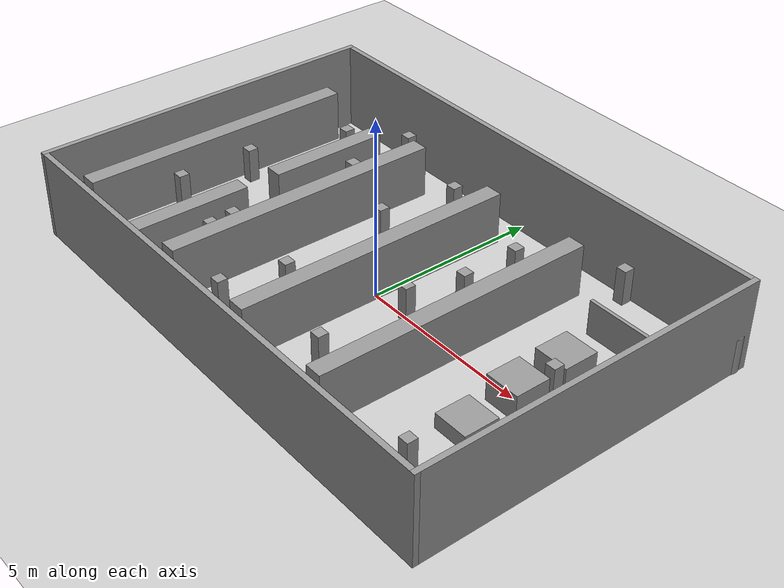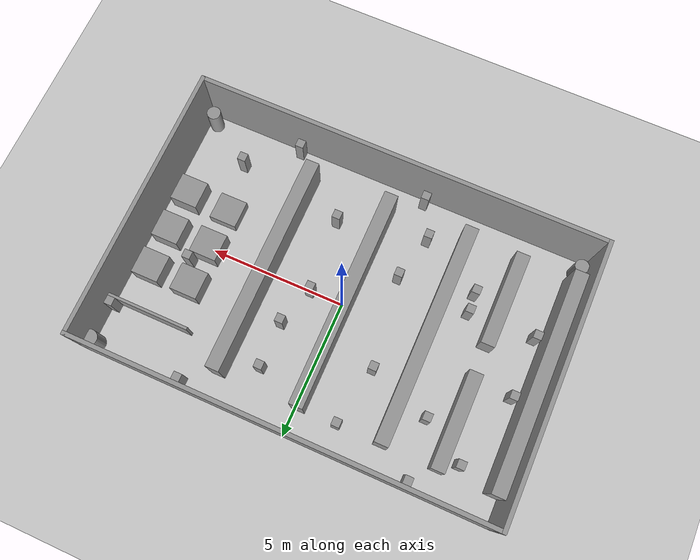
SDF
<sdf version="1.7">
 <world name="default">
  <light name="sun" type="directional">
   <pose>0 0 10 0 -0 0</pose>
   <diffuse>0.8 0.8 0.8 1</diffuse>
   <specular>0.2 0.2 0.2 1</specular>
   <attenuation>
    <range>1000</range>
    <constant>0.9</constant>
    <linear>0.01</linear>
    <quadratic>0.001</quadratic>
   </attenuation>
   <direction>-0.5 0.1 -0.9</direction>
   <spot><inner_angle>0</inner_angle><outer_angle>0</outer_angle><falloff>0</falloff></spot>
  </light>
  <model name="ground_plane">
   <static>1</static>
   <link name="link">
    <collision name="collision">
     <geometry><plane><normal>0 0 1</normal><size>100 100</size></plane></geometry>
     <surface>
      <contact><collide_bitmask>65535</collide_bitmask></contact>
      <friction><ode><mu>100</mu><mu2>50</mu2></ode></friction>
     </surface>
    </collision>
    <visual name="visual">
     <cast_shadows>0</cast_shadows>
     <geometry><plane><normal>0 0 1</normal><size>100 100</size></plane></geometry>
     <material>
      <script><uri>file://media/materials/scripts/gazebo.material</uri><name>Gazebo/Grey</name></script>
     </material>
    </visual>
   </link>
  </model>
  <gravity>0 0 -9.8</gravity>
  <magnetic_field>6e-06 2.3e-05 -4.2e-05</magnetic_field>
  <atmosphere type="adiabatic"/>
  <physics type="ode">
   <max_step_size>0.001</max_step_size>
   <real_time_factor>1</real_time_factor>
   <real_time_update_rate>1000</real_time_update_rate>
  </physics>
  <scene><ambient>0.4 0.4 0.4 1</ambient><background>0.7 0.7 0.7 1</background><shadows>1</shadows></scene>
  <spherical_coordinates>
   <surface_model>EARTH_WGS84</surface_model>
   <latitude_deg>0</latitude_deg>
   <longitude_deg>0</longitude_deg>
   <elevation>0</elevation>
   <heading_deg>0</heading_deg>
  </spherical_coordinates>
  <model name="model_wall">
   <link name="Wall_0">
    <collision name="Wall_0_Collision">
     <geometry><box><size>10 0.15 2.5</size></box></geometry>
     <pose>0 0 1.25 0 -0 0</pose>
    </collision>
    <visual name="Wall_0_Visual">
     <pose>0 0 1.25 0 -0 0</pose>
     <geometry><box><size>10 0.15 2.5</size></box></geometry>
     <material>
      <script><uri>file://media/materials/scripts/gazebo.material</uri><name>Gazebo/Grey</name></script>
      <ambient>1 1 1 1</ambient>
     </material>
     <meta><layer>0</layer></meta>
    </visual>
    <pose>-7.425 0 0 0 -0 1.5708</pose>
   </link>
   <link name="Wall_4">
    <collision name="Wall_4_Collision">
     <geometry><box><size>15 0.15 2.5</size></box></geometry>
     <pose>0 0 1.25 0 -0 0</pose>
    </collision>
    <visual name="Wall_4_Visual">
     <pose>0 0 1.25 0 -0 0</pose>
     <geometry><box><size>15 0.15 2.5</size></box></geometry>
     <material>
      <script><uri>file://media/materials/scripts/gazebo.material</uri><name>Gazebo/Grey</name></script>
      <ambient>1 1 1 1</ambient>
     </material>
     <meta><layer>0</layer></meta>
    </visual>
    <pose>0 4.925 0 0 -0 0</pose>
   </link>
   <link name="Wall_7">
    <collision name="Wall_7_Collision">
     <geometry><box><size>10 0.15 2.5</size></box></geometry>
     <pose>0 0 1.25 0 -0 0</pose>
    </collision>
    <visual name="Wall_7_Visual">
     <pose>0 0 1.25 0 -0 0</pose>
     <geometry><box><size>10 0.15 2.5</size></box></geometry>
     <material>
      <script><uri>file://media/materials/scripts/gazebo.material</uri><name>Gazebo/Grey</name></script>
      <ambient>1 1 1 1</ambient>
     </material>
     <meta><layer>0</layer></meta>
    </visual>
    <pose>7.425 0 0 0 -0 -1.5708</pose>
   </link>
   <link name="Wall_8">
    <collision name="Wall_8_Collision">
     <geometry><box><size>15 0.15 2.5</size></box></geometry>
     <pose>0 0 1.25 0 -0 0</pose>
    </collision>
    <visual name="Wall_8_Visual">
     <pose>0 0 1.25 0 -0 0</pose>
     <geometry><box><size>15 0.15 2.5</size></box></geometry>
     <material>
      <script><uri>file://media/materials/scripts/gazebo.material</uri><name>Gazebo/Grey</name></script>
      <ambient>1 1 1 1</ambient>
     </material>
     <meta><layer>0</layer></meta>
    </visual>
    <pose>0 -4.925 0 0 -0 3.14159</pose>
   </link>
   <static>1</static>
  </model>
  <model name="Untitled">
   <link name="link_0">
    <inertial>
     <mass>1000</mass>
     <inertia><ixx>1666.67</ixx><ixy>0</ixy><ixz>0</ixz><iyy>1666.67</iyy><iyz>0</iyz><izz>1666.67</izz></inertia>
    </inertial>
    <pose>-7.1 0 0.75 0 -0 0</pose>
    <visual name="visual">
     <geometry><box><size>0.5 8 1.5</size></box></geometry>
     <material>
      <lighting>1</lighting>
      <script><uri>file://media/materials/scripts/gazebo.material</uri><name>Gazebo/Grey</name></script>
      <shader type="pixel"><normal_map>__default__</normal_map></shader>
      <ambient>0.3 0.3 0.3 1</ambient>
      <diffuse>0.7 0.7 0.7 1</diffuse>
      <specular>0.01 0.01 0.01 1</specular>
      <emissive>0 0 0 1</emissive>
     </material>
    </visual>
    <collision name="collision">
     <geometry><box><size>0.5 8 1.5</size></box></geometry>
     <surface>
      <friction>
       <ode><mu>1</mu><mu2>1</mu2><fdir1>0 0 0</fdir1><slip1>1</slip1><slip2>1</slip2></ode>
       <torsional>
        <coefficient>1</coefficient>
        <patch_radius>0</patch_radius>
        <surface_radius>0</surface_radius>
        <use_patch_radius>1</use_patch_radius>
        <ode><slip>0</slip></ode>
       </torsional>
      </friction>
      <bounce><restitution_coefficient>0</restitution_coefficient><threshold>1e+06</threshold></bounce>
      <contact>
       <collide_without_contact>0</collide_without_contact>
       <collide_without_contact_bitmask>1</collide_without_contact_bitmask>
       <collide_bitmask>1</collide_bitmask>
       <ode>
        <soft_cfm>0</soft_cfm>
        <soft_erp>0.2</soft_erp>
        <kp>1e+13</kp>
        <kd>1</kd>
        <max_vel>0.01</max_vel>
        <min_depth>0</min_depth>
       </ode>
       <bullet>
        <split_impulse>1</split_impulse>
        <split_impulse_penetration_threshold>-0.01</split_impulse_penetration_threshold>
        <soft_cfm>0</soft_cfm>
        <soft_erp>0.2</soft_erp>
        <kp>1e+13</kp>
        <kd>1</kd>
       </bullet>
      </contact>
     </surface>
    </collision>
   </link>
   <link name="link_1">
    <inertial>
     <mass>1000</mass>
     <inertia><ixx>1666.67</ixx><ixy>0</ixy><ixz>0</ixz><iyy>1666.67</iyy><iyz>0</iyz><izz>1666.67</izz></inertia>
    </inertial>
    <pose>-5.125 2.25 0.5 0 -0 0</pose>
    <visual name="visual">
     <geometry><box><size>0.5 3.5 1</size></box></geometry>
     <material>
      <lighting>1</lighting>
      <script><uri>file://media/materials/scripts/gazebo.material</uri><name>Gazebo/Grey</name></script>
      <shader type="pixel"><normal_map>__default__</normal_map></shader>
      <ambient>0.3 0.3 0.3 1</ambient>
      <diffuse>0.7 0.7 0.7 1</diffuse>
      <specular>0.01 0.01 0.01 1</specular>
      <emissive>0 0 0 1</emissive>
     </material>
    </visual>
    <collision name="collision">
     <geometry><box><size>0.5 3.5 1</size></box></geometry>
     <surface>
      <friction>
       <ode><mu>1</mu><mu2>1</mu2><fdir1>0 0 0</fdir1><slip1>1</slip1><slip2>1</slip2></ode>
       <torsional>
        <coefficient>1</coefficient>
        <patch_radius>0</patch_radius>
        <surface_radius>0</surface_radius>
        <use_patch_radius>1</use_patch_radius>
        <ode><slip>0</slip></ode>
       </torsional>
      </friction>
      <bounce><restitution_coefficient>0</restitution_coefficient><threshold>1e+06</threshold></bounce>
      <contact>
       <collide_without_contact>0</collide_without_contact>
       <collide_without_contact_bitmask>1</collide_without_contact_bitmask>
       <collide_bitmask>1</collide_bitmask>
       <ode>
        <soft_cfm>0</soft_cfm>
        <soft_erp>0.2</soft_erp>
        <kp>1e+13</kp>
        <kd>1</kd>
        <max_vel>0.01</max_vel>
        <min_depth>0</min_depth>
       </ode>
       <bullet>
        <split_impulse>1</split_impulse>
        <split_impulse_penetration_threshold>-0.01</split_impulse_penetration_threshold>
        <soft_cfm>0</soft_cfm>
        <soft_erp>0.2</soft_erp>
        <kp>1e+13</kp>
        <kd>1</kd>
       </bullet>
      </contact>
     </surface>
    </collision>
   </link>
   <link name="link_10">
    <inertial>
     <mass>1000</mass>
     <inertia><ixx>1666.67</ixx><ixy>0</ixy><ixz>0</ixz><iyy>1666.67</iyy><iyz>0</iyz><izz>1666.67</izz></inertia>
    </inertial>
    <pose>5.125 -1.5 0.0375 0 -0 0</pose>
    <visual name="visual">
     <geometry><box><size>1 1 0.75</size></box></geometry>
     <material>
      <lighting>1</lighting>
      <script><uri>file://media/materials/scripts/gazebo.material</uri><name>Gazebo/Grey</name></script>
      <shader type="pixel"><normal_map>__default__</normal_map></shader>
      <ambient>0.3 0.3 0.3 1</ambient>
      <diffuse>0.7 0.7 0.7 1</diffuse>
      <specular>0.01 0.01 0.01 1</specular>
      <emissive>0 0 0 1</emissive>
     </material>
    </visual>
    <collision name="collision">
     <geometry><box><size>1 1 0.75</size></box></geometry>
     <surface>
      <friction>
       <ode><mu>1</mu><mu2>1</mu2><fdir1>0 0 0</fdir1><slip1>1</slip1><slip2>1</slip2></ode>
       <torsional>
        <coefficient>1</coefficient>
        <patch_radius>0</patch_radius>
        <surface_radius>0</surface_radius>
        <use_patch_radius>1</use_patch_radius>
        <ode><slip>0</slip></ode>
       </torsional>
      </friction>
      <bounce><restitution_coefficient>0</restitution_coefficient><threshold>1e+06</threshold></bounce>
      <contact>
       <collide_without_contact>0</collide_without_contact>
       <collide_without_contact_bitmask>1</collide_without_contact_bitmask>
       <collide_bitmask>1</collide_bitmask>
       <ode>
        <soft_cfm>0</soft_cfm>
        <soft_erp>0.2</soft_erp>
        <kp>1e+13</kp>
        <kd>1</kd>
        <max_vel>0.01</max_vel>
        <min_depth>0</min_depth>
       </ode>
       <bullet>
        <split_impulse>1</split_impulse>
        <split_impulse_penetration_threshold>-0.01</split_impulse_penetration_threshold>
        <soft_cfm>0</soft_cfm>
        <soft_erp>0.2</soft_erp>
        <kp>1e+13</kp>
        <kd>1</kd>
       </bullet>
      </contact>
     </surface>
    </collision>
   </link>
   <link name="link_11">
    <inertial>
     <mass>1000</mass>
     <inertia><ixx>1666.67</ixx><ixy>0</ixy><ixz>0</ixz><iyy>1666.67</iyy><iyz>0</iyz><izz>1666.67</izz></inertia>
    </inertial>
    <pose>6.625 -1.5 0.375 0 -0 0</pose>
    <visual name="visual">
     <geometry><box><size>1 1 0.75</size></box></geometry>
     <material>
      <lighting>1</lighting>
      <script><uri>file://media/materials/scripts/gazebo.material</uri><name>Gazebo/Grey</name></script>
      <shader type="pixel"><normal_map>__default__</normal_map></shader>
      <ambient>0.3 0.3 0.3 1</ambient>
      <diffuse>0.7 0.7 0.7 1</diffuse>
      <specular>0.01 0.01 0.01 1</specular>
      <emissive>0 0 0 1</emissive>
     </material>
    </visual>
    <collision name="collision">
     <geometry><box><size>1 1 0.75</size></box></geometry>
     <surface>
      <friction>
       <ode><mu>1</mu><mu2>1</mu2><fdir1>0 0 0</fdir1><slip1>1</slip1><slip2>1</slip2></ode>
       <torsional>
        <coefficient>1</coefficient>
        <patch_radius>0</patch_radius>
        <surface_radius>0</surface_radius>
        <use_patch_radius>1</use_patch_radius>
        <ode><slip>0</slip></ode>
       </torsional>
      </friction>
      <bounce><restitution_coefficient>0</restitution_coefficient><threshold>1e+06</threshold></bounce>
      <contact>
       <collide_without_contact>0</collide_without_contact>
       <collide_without_contact_bitmask>1</collide_without_contact_bitmask>
       <collide_bitmask>1</collide_bitmask>
       <ode>
        <soft_cfm>0</soft_cfm>
        <soft_erp>0.2</soft_erp>
        <kp>1e+13</kp>
        <kd>1</kd>
        <max_vel>0.01</max_vel>
        <min_depth>0</min_depth>
       </ode>
       <bullet>
        <split_impulse>1</split_impulse>
        <split_impulse_penetration_threshold>-0.01</split_impulse_penetration_threshold>
        <soft_cfm>0</soft_cfm>
        <soft_erp>0.2</soft_erp>
        <kp>1e+13</kp>
        <kd>1</kd>
       </bullet>
      </contact>
     </surface>
    </collision>
   </link>
   <link name="link_2">
    <inertial>
     <mass>1000</mass>
     <inertia><ixx>1666.67</ixx><ixy>0</ixy><ixz>0</ixz><iyy>1666.67</iyy><iyz>0</iyz><izz>1666.67</izz></inertia>
    </inertial>
    <pose>-5.125 -2.25 0.5 0 -0 0</pose>
    <visual name="visual">
     <geometry><box><size>0.5 3.5 1</size></box></geometry>
     <material>
      <lighting>1</lighting>
      <script><uri>file://media/materials/scripts/gazebo.material</uri><name>Gazebo/Grey</name></script>
      <shader type="pixel"><normal_map>__default__</normal_map></shader>
      <ambient>0.3 0.3 0.3 1</ambient>
      <diffuse>0.7 0.7 0.7 1</diffuse>
      <specular>0.01 0.01 0.01 1</specular>
      <emissive>0 0 0 1</emissive>
     </material>
    </visual>
    <collision name="collision">
     <geometry><box><size>0.5 3.5 1</size></box></geometry>
     <surface>
      <friction>
       <ode><mu>1</mu><mu2>1</mu2><fdir1>0 0 0</fdir1><slip1>1</slip1><slip2>1</slip2></ode>
       <torsional>
        <coefficient>1</coefficient>
        <patch_radius>0</patch_radius>
        <surface_radius>0</surface_radius>
        <use_patch_radius>1</use_patch_radius>
        <ode><slip>0</slip></ode>
       </torsional>
      </friction>
      <bounce><restitution_coefficient>0</restitution_coefficient><threshold>1e+06</threshold></bounce>
      <contact>
       <collide_without_contact>0</collide_without_contact>
       <collide_without_contact_bitmask>1</collide_without_contact_bitmask>
       <collide_bitmask>1</collide_bitmask>
       <ode>
        <soft_cfm>0</soft_cfm>
        <soft_erp>0.2</soft_erp>
        <kp>1e+13</kp>
        <kd>1</kd>
        <max_vel>0.01</max_vel>
        <min_depth>0</min_depth>
       </ode>
       <bullet>
        <split_impulse>1</split_impulse>
        <split_impulse_penetration_threshold>-0.01</split_impulse_penetration_threshold>
        <soft_cfm>0</soft_cfm>
        <soft_erp>0.2</soft_erp>
        <kp>1e+13</kp>
        <kd>1</kd>
       </bullet>
      </contact>
     </surface>
    </collision>
   </link>
   <link name="link_3">
    <inertial>
     <mass>1000</mass>
     <inertia><ixx>1666.67</ixx><ixy>0</ixy><ixz>0</ixz><iyy>1666.67</iyy><iyz>0</iyz><izz>1666.67</izz></inertia>
    </inertial>
    <pose>-3.125 0 0.75 0 -0 0</pose>
    <visual name="visual">
     <geometry><box><size>0.5 8 1.5</size></box></geometry>
     <material>
      <lighting>1</lighting>
      <script><uri>file://media/materials/scripts/gazebo.material</uri><name>Gazebo/Grey</name></script>
      <shader type="pixel"><normal_map>__default__</normal_map></shader>
      <ambient>0.3 0.3 0.3 1</ambient>
      <diffuse>0.7 0.7 0.7 1</diffuse>
      <specular>0.01 0.01 0.01 1</specular>
      <emissive>0 0 0 1</emissive>
     </material>
    </visual>
    <collision name="collision">
     <geometry><box><size>0.5 8 1.5</size></box></geometry>
     <surface>
      <friction>
       <ode><mu>1</mu><mu2>1</mu2><fdir1>0 0 0</fdir1><slip1>1</slip1><slip2>1</slip2></ode>
       <torsional>
        <coefficient>1</coefficient>
        <patch_radius>0</patch_radius>
        <surface_radius>0</surface_radius>
        <use_patch_radius>1</use_patch_radius>
        <ode><slip>0</slip></ode>
       </torsional>
      </friction>
      <bounce><restitution_coefficient>0</restitution_coefficient><threshold>1e+06</threshold></bounce>
      <contact>
       <collide_without_contact>0</collide_without_contact>
       <collide_without_contact_bitmask>1</collide_without_contact_bitmask>
       <collide_bitmask>1</collide_bitmask>
       <ode>
        <soft_cfm>0</soft_cfm>
        <soft_erp>0.2</soft_erp>
        <kp>1e+13</kp>
        <kd>1</kd>
        <max_vel>0.01</max_vel>
        <min_depth>0</min_depth>
       </ode>
       <bullet>
        <split_impulse>1</split_impulse>
        <split_impulse_penetration_threshold>-0.01</split_impulse_penetration_threshold>
        <soft_cfm>0</soft_cfm>
        <soft_erp>0.2</soft_erp>
        <kp>1e+13</kp>
        <kd>1</kd>
       </bullet>
      </contact>
     </surface>
    </collision>
   </link>
   <link name="link_4">
    <inertial>
     <mass>1000</mass>
     <inertia><ixx>1666.67</ixx><ixy>0</ixy><ixz>0</ixz><iyy>1666.67</iyy><iyz>0</iyz><izz>1666.67</izz></inertia>
    </inertial>
    <pose>-0.125 0 0.75 0 -0 0</pose>
    <visual name="visual">
     <geometry><box><size>0.5 8 1.5</size></box></geometry>
     <material>
      <lighting>1</lighting>
      <script><uri>file://media/materials/scripts/gazebo.material</uri><name>Gazebo/Grey</name></script>
      <shader type="pixel"><normal_map>__default__</normal_map></shader>
      <ambient>0.3 0.3 0.3 1</ambient>
      <diffuse>0.7 0.7 0.7 1</diffuse>
      <specular>0.01 0.01 0.01 1</specular>
      <emissive>0 0 0 1</emissive>
     </material>
    </visual>
    <collision name="collision">
     <geometry><box><size>0.5 8 1.5</size></box></geometry>
     <surface>
      <friction>
       <ode><mu>1</mu><mu2>1</mu2><fdir1>0 0 0</fdir1><slip1>1</slip1><slip2>1</slip2></ode>
       <torsional>
        <coefficient>1</coefficient>
        <patch_radius>0</patch_radius>
        <surface_radius>0</surface_radius>
        <use_patch_radius>1</use_patch_radius>
        <ode><slip>0</slip></ode>
       </torsional>
      </friction>
      <bounce><restitution_coefficient>0</restitution_coefficient><threshold>1e+06</threshold></bounce>
      <contact>
       <collide_without_contact>0</collide_without_contact>
       <collide_without_contact_bitmask>1</collide_without_contact_bitmask>
       <collide_bitmask>1</collide_bitmask>
       <ode>
        <soft_cfm>0</soft_cfm>
        <soft_erp>0.2</soft_erp>
        <kp>1e+13</kp>
        <kd>1</kd>
        <max_vel>0.01</max_vel>
        <min_depth>0</min_depth>
       </ode>
       <bullet>
        <split_impulse>1</split_impulse>
        <split_impulse_penetration_threshold>-0.01</split_impulse_penetration_threshold>
        <soft_cfm>0</soft_cfm>
        <soft_erp>0.2</soft_erp>
        <kp>1e+13</kp>
        <kd>1</kd>
       </bullet>
      </contact>
     </surface>
    </collision>
   </link>
   <link name="link_5">
    <inertial>
     <mass>1000</mass>
     <inertia><ixx>1666.67</ixx><ixy>0</ixy><ixz>0</ixz><iyy>1666.67</iyy><iyz>0</iyz><izz>1666.67</izz></inertia>
    </inertial>
    <pose>2.875 0 0.75 0 -0 0</pose>
    <visual name="visual">
     <geometry><box><size>0.5 8 1.5</size></box></geometry>
     <material>
      <lighting>1</lighting>
      <script><uri>file://media/materials/scripts/gazebo.material</uri><name>Gazebo/Grey</name></script>
      <shader type="pixel"><normal_map>__default__</normal_map></shader>
      <ambient>0.3 0.3 0.3 1</ambient>
      <diffuse>0.7 0.7 0.7 1</diffuse>
      <specular>0.01 0.01 0.01 1</specular>
      <emissive>0 0 0 1</emissive>
     </material>
    </visual>
    <collision name="collision">
     <geometry><box><size>0.5 8 1.5</size></box></geometry>
     <surface>
      <friction>
       <ode><mu>1</mu><mu2>1</mu2><fdir1>0 0 0</fdir1><slip1>1</slip1><slip2>1</slip2></ode>
       <torsional>
        <coefficient>1</coefficient>
        <patch_radius>0</patch_radius>
        <surface_radius>0</surface_radius>
        <use_patch_radius>1</use_patch_radius>
        <ode><slip>0</slip></ode>
       </torsional>
      </friction>
      <bounce><restitution_coefficient>0</restitution_coefficient><threshold>1e+06</threshold></bounce>
      <contact>
       <collide_without_contact>0</collide_without_contact>
       <collide_without_contact_bitmask>1</collide_without_contact_bitmask>
       <collide_bitmask>1</collide_bitmask>
       <ode>
        <soft_cfm>0</soft_cfm>
        <soft_erp>0.2</soft_erp>
        <kp>1e+13</kp>
        <kd>1</kd>
        <max_vel>0.01</max_vel>
        <min_depth>0</min_depth>
       </ode>
       <bullet>
        <split_impulse>1</split_impulse>
        <split_impulse_penetration_threshold>-0.01</split_impulse_penetration_threshold>
        <soft_cfm>0</soft_cfm>
        <soft_erp>0.2</soft_erp>
        <kp>1e+13</kp>
        <kd>1</kd>
       </bullet>
      </contact>
     </surface>
    </collision>
   </link>
   <link name="link_6">
    <inertial>
     <mass>1000</mass>
     <inertia><ixx>1666.67</ixx><ixy>0</ixy><ixz>0</ixz><iyy>1666.67</iyy><iyz>0</iyz><izz>1666.67</izz></inertia>
    </inertial>
    <pose>5.125 0 0.375 0 -0 0</pose>
    <visual name="visual">
     <geometry><box><size>1 1 0.75</size></box></geometry>
     <material>
      <lighting>1</lighting>
      <script><uri>file://media/materials/scripts/gazebo.material</uri><name>Gazebo/Grey</name></script>
      <shader type="pixel"><normal_map>__default__</normal_map></shader>
      <ambient>0.3 0.3 0.3 1</ambient>
      <diffuse>0.7 0.7 0.7 1</diffuse>
      <specular>0.01 0.01 0.01 1</specular>
      <emissive>0 0 0 1</emissive>
     </material>
    </visual>
    <collision name="collision">
     <geometry><box><size>1 1 0.75</size></box></geometry>
     <surface>
      <friction>
       <ode><mu>1</mu><mu2>1</mu2><fdir1>0 0 0</fdir1><slip1>1</slip1><slip2>1</slip2></ode>
       <torsional>
        <coefficient>1</coefficient>
        <patch_radius>0</patch_radius>
        <surface_radius>0</surface_radius>
        <use_patch_radius>1</use_patch_radius>
        <ode><slip>0</slip></ode>
       </torsional>
      </friction>
      <bounce><restitution_coefficient>0</restitution_coefficient><threshold>1e+06</threshold></bounce>
      <contact>
       <collide_without_contact>0</collide_without_contact>
       <collide_without_contact_bitmask>1</collide_without_contact_bitmask>
       <collide_bitmask>1</collide_bitmask>
       <ode>
        <soft_cfm>0</soft_cfm>
        <soft_erp>0.2</soft_erp>
        <kp>1e+13</kp>
        <kd>1</kd>
        <max_vel>0.01</max_vel>
        <min_depth>0</min_depth>
       </ode>
       <bullet>
        <split_impulse>1</split_impulse>
        <split_impulse_penetration_threshold>-0.01</split_impulse_penetration_threshold>
        <soft_cfm>0</soft_cfm>
        <soft_erp>0.2</soft_erp>
        <kp>1e+13</kp>
        <kd>1</kd>
       </bullet>
      </contact>
     </surface>
    </collision>
   </link>
   <link name="link_7">
    <inertial>
     <mass>1000</mass>
     <inertia><ixx>1666.67</ixx><ixy>0</ixy><ixz>0</ixz><iyy>1666.67</iyy><iyz>0</iyz><izz>1666.67</izz></inertia>
    </inertial>
    <pose>6.625 0 0.375 0 -0 0</pose>
    <visual name="visual">
     <geometry><box><size>1 1 0.75</size></box></geometry>
     <material>
      <lighting>1</lighting>
      <script><uri>file://media/materials/scripts/gazebo.material</uri><name>Gazebo/Grey</name></script>
      <shader type="pixel"><normal_map>__default__</normal_map></shader>
      <ambient>0.3 0.3 0.3 1</ambient>
      <diffuse>0.7 0.7 0.7 1</diffuse>
      <specular>0.01 0.01 0.01 1</specular>
      <emissive>0 0 0 1</emissive>
     </material>
    </visual>
    <collision name="collision">
     <geometry><box><size>1 1 0.75</size></box></geometry>
     <surface>
      <friction>
       <ode><mu>1</mu><mu2>1</mu2><fdir1>0 0 0</fdir1><slip1>1</slip1><slip2>1</slip2></ode>
       <torsional>
        <coefficient>1</coefficient>
        <patch_radius>0</patch_radius>
        <surface_radius>0</surface_radius>
        <use_patch_radius>1</use_patch_radius>
        <ode><slip>0</slip></ode>
       </torsional>
      </friction>
      <bounce><restitution_coefficient>0</restitution_coefficient><threshold>1e+06</threshold></bounce>
      <contact>
       <collide_without_contact>0</collide_without_contact>
       <collide_without_contact_bitmask>1</collide_without_contact_bitmask>
       <collide_bitmask>1</collide_bitmask>
       <ode>
        <soft_cfm>0</soft_cfm>
        <soft_erp>0.2</soft_erp>
        <kp>1e+13</kp>
        <kd>1</kd>
        <max_vel>0.01</max_vel>
        <min_depth>0</min_depth>
       </ode>
       <bullet>
        <split_impulse>1</split_impulse>
        <split_impulse_penetration_threshold>-0.01</split_impulse_penetration_threshold>
        <soft_cfm>0</soft_cfm>
        <soft_erp>0.2</soft_erp>
        <kp>1e+13</kp>
        <kd>1</kd>
       </bullet>
      </contact>
     </surface>
    </collision>
   </link>
   <link name="link_8">
    <inertial>
     <mass>1000</mass>
     <inertia><ixx>1666.67</ixx><ixy>0</ixy><ixz>0</ixz><iyy>1666.67</iyy><iyz>0</iyz><izz>1666.67</izz></inertia>
    </inertial>
    <pose>5.125 1.5 0.375 0 -0 0</pose>
    <visual name="visual">
     <geometry><box><size>1 1 0.75</size></box></geometry>
     <material>
      <lighting>1</lighting>
      <script><uri>file://media/materials/scripts/gazebo.material</uri><name>Gazebo/Grey</name></script>
      <shader type="pixel"><normal_map>__default__</normal_map></shader>
      <ambient>0.3 0.3 0.3 1</ambient>
      <diffuse>0.7 0.7 0.7 1</diffuse>
      <specular>0.01 0.01 0.01 1</specular>
      <emissive>0 0 0 1</emissive>
     </material>
    </visual>
    <collision name="collision">
     <geometry><box><size>1 1 0.75</size></box></geometry>
     <surface>
      <friction>
       <ode><mu>1</mu><mu2>1</mu2><fdir1>0 0 0</fdir1><slip1>1</slip1><slip2>1</slip2></ode>
       <torsional>
        <coefficient>1</coefficient>
        <patch_radius>0</patch_radius>
        <surface_radius>0</surface_radius>
        <use_patch_radius>1</use_patch_radius>
        <ode><slip>0</slip></ode>
       </torsional>
      </friction>
      <bounce><restitution_coefficient>0</restitution_coefficient><threshold>1e+06</threshold></bounce>
      <contact>
       <collide_without_contact>0</collide_without_contact>
       <collide_without_contact_bitmask>1</collide_without_contact_bitmask>
       <collide_bitmask>1</collide_bitmask>
       <ode>
        <soft_cfm>0</soft_cfm>
        <soft_erp>0.2</soft_erp>
        <kp>1e+13</kp>
        <kd>1</kd>
        <max_vel>0.01</max_vel>
        <min_depth>0</min_depth>
       </ode>
       <bullet>
        <split_impulse>1</split_impulse>
        <split_impulse_penetration_threshold>-0.01</split_impulse_penetration_threshold>
        <soft_cfm>0</soft_cfm>
        <soft_erp>0.2</soft_erp>
        <kp>1e+13</kp>
        <kd>1</kd>
       </bullet>
      </contact>
     </surface>
    </collision>
   </link>
   <link name="link_9">
    <inertial>
     <mass>1000</mass>
     <inertia><ixx>1666.67</ixx><ixy>0</ixy><ixz>0</ixz><iyy>1666.67</iyy><iyz>0</iyz><izz>1666.67</izz></inertia>
    </inertial>
    <pose>6.625 1.5 0.375 0 -0 0</pose>
    <visual name="visual">
     <geometry><box><size>1 1 0.75</size></box></geometry>
     <material>
      <lighting>1</lighting>
      <script><uri>file://media/materials/scripts/gazebo.material</uri><name>Gazebo/Grey</name></script>
      <shader type="pixel"><normal_map>__default__</normal_map></shader>
      <ambient>0.3 0.3 0.3 1</ambient>
      <diffuse>0.7 0.7 0.7 1</diffuse>
      <specular>0.01 0.01 0.01 1</specular>
      <emissive>0 0 0 1</emissive>
     </material>
    </visual>
    <collision name="collision">
     <geometry><box><size>1 1 0.75</size></box></geometry>
     <surface>
      <friction>
       <ode><mu>1</mu><mu2>1</mu2><fdir1>0 0 0</fdir1><slip1>1</slip1><slip2>1</slip2></ode>
       <torsional>
        <coefficient>1</coefficient>
        <patch_radius>0</patch_radius>
        <surface_radius>0</surface_radius>
        <use_patch_radius>1</use_patch_radius>
        <ode><slip>0</slip></ode>
       </torsional>
      </friction>
      <bounce><restitution_coefficient>0</restitution_coefficient><threshold>1e+06</threshold></bounce>
      <contact>
       <collide_without_contact>0</collide_without_contact>
       <collide_without_contact_bitmask>1</collide_without_contact_bitmask>
       <collide_bitmask>1</collide_bitmask>
       <ode>
        <soft_cfm>0</soft_cfm>
        <soft_erp>0.2</soft_erp>
        <kp>1e+13</kp>
        <kd>1</kd>
        <max_vel>0.01</max_vel>
        <min_depth>0</min_depth>
       </ode>
       <bullet>
        <split_impulse>1</split_impulse>
        <split_impulse_penetration_threshold>-0.01</split_impulse_penetration_threshold>
        <soft_cfm>0</soft_cfm>
        <soft_erp>0.2</soft_erp>
        <kp>1e+13</kp>
        <kd>1</kd>
       </bullet>
      </contact>
     </surface>
    </collision>
   </link>
   <static>0</static>
   <pose>1.1e-05 0.000748 -9e-06 1e-06 1e-06 3e-06</pose>
  </model>
  <model name="model_people">
   <link name="link_1">
    <inertial>
     <mass>1000</mass>
     <inertia><ixx>1666.67</ixx><ixy>0</ixy><ixz>0</ixz><iyy>1666.67</iyy><iyz>0</iyz><izz>1666.67</izz></inertia>
    </inertial>
    <pose>5.87565 3.29526 0 0 -0 0</pose>
    <visual name="visual">
     <geometry><box><size>3 0.1 1</size></box></geometry>
     <material>
      <lighting>1</lighting>
      <script><uri>file://media/materials/scripts/gazebo.material</uri><name>Gazebo/Grey</name></script>
      <shader type="pixel"><normal_map>__default__</normal_map></shader>
      <ambient>0.3 0.3 0.3 1</ambient>
      <diffuse>0.7 0.7 0.7 1</diffuse>
      <specular>0.01 0.01 0.01 1</specular>
      <emissive>0 0 0 1</emissive>
     </material>
    </visual>
    <collision name="collision">
     <geometry><box><size>3 0.1 1</size></box></geometry>
     <surface>
      <friction>
       <ode><mu>1</mu><mu2>1</mu2><fdir1>0 0 0</fdir1><slip1>1</slip1><slip2>1</slip2></ode>
       <torsional>
        <coefficient>1</coefficient>
        <patch_radius>0</patch_radius>
        <surface_radius>0</surface_radius>
        <use_patch_radius>1</use_patch_radius>
        <ode><slip>0</slip></ode>
       </torsional>
      </friction>
      <bounce><restitution_coefficient>0</restitution_coefficient><threshold>1e+06</threshold></bounce>
      <contact>
       <collide_without_contact>0</collide_without_contact>
       <collide_without_contact_bitmask>1</collide_without_contact_bitmask>
       <collide_bitmask>1</collide_bitmask>
       <ode>
        <soft_cfm>0</soft_cfm>
        <soft_erp>0.2</soft_erp>
        <kp>1e+13</kp>
        <kd>1</kd>
        <max_vel>0.01</max_vel>
        <min_depth>0</min_depth>
       </ode>
       <bullet>
        <split_impulse>1</split_impulse>
        <split_impulse_penetration_threshold>-0.01</split_impulse_penetration_threshold>
        <soft_cfm>0</soft_cfm>
        <soft_erp>0.2</soft_erp>
        <kp>1e+13</kp>
        <kd>1</kd>
       </bullet>
      </contact>
     </surface>
    </collision>
   </link>
   <link name="link_3">
    <inertial>
     <mass>1000</mass>
     <inertia><ixx>1666.67</ixx><ixy>0</ixy><ixz>0</ixz><iyy>1666.67</iyy><iyz>0</iyz><izz>1666.67</izz></inertia>
    </inertial>
    <pose>1.41254 -2.50014 0 0 -0 0</pose>
    <visual name="visual">
     <geometry><box><size>0.3 0.3 1</size></box></geometry>
     <material>
      <lighting>1</lighting>
      <script><uri>file://media/materials/scripts/gazebo.material</uri><name>Gazebo/Grey</name></script>
      <shader type="pixel"><normal_map>__default__</normal_map></shader>
      <ambient>0.3 0.3 0.3 1</ambient>
      <diffuse>0.7 0.7 0.7 1</diffuse>
      <specular>0.01 0.01 0.01 1</specular>
      <emissive>0 0 0 1</emissive>
     </material>
    </visual>
    <collision name="collision">
     <geometry><box><size>0.3 0.3 1</size></box></geometry>
     <surface>
      <friction>
       <ode><mu>1</mu><mu2>1</mu2><fdir1>0 0 0</fdir1><slip1>1</slip1><slip2>1</slip2></ode>
       <torsional>
        <coefficient>1</coefficient>
        <patch_radius>0</patch_radius>
        <surface_radius>0</surface_radius>
        <use_patch_radius>1</use_patch_radius>
        <ode><slip>0</slip></ode>
       </torsional>
      </friction>
      <bounce><restitution_coefficient>0</restitution_coefficient><threshold>1e+06</threshold></bounce>
      <contact>
       <collide_without_contact>0</collide_without_contact>
       <collide_without_contact_bitmask>1</collide_without_contact_bitmask>
       <collide_bitmask>1</collide_bitmask>
       <ode>
        <soft_cfm>0</soft_cfm>
        <soft_erp>0.2</soft_erp>
        <kp>1e+13</kp>
        <kd>1</kd>
        <max_vel>0.01</max_vel>
        <min_depth>0</min_depth>
       </ode>
       <bullet>
        <split_impulse>1</split_impulse>
        <split_impulse_penetration_threshold>-0.01</split_impulse_penetration_threshold>
        <soft_cfm>0</soft_cfm>
        <soft_erp>0.2</soft_erp>
        <kp>1e+13</kp>
        <kd>1</kd>
       </bullet>
      </contact>
     </surface>
    </collision>
   </link>
   <link name="link_3_clone">
    <inertial>
     <mass>1</mass>
     <inertia><ixx>1666.67</ixx><ixy>0</ixy><ixz>0</ixz><iyy>1666.67</iyy><iyz>0</iyz><izz>1666.67</izz></inertia>
    </inertial>
    <pose>5.41108 -3.14206 0 0 -0 0</pose>
    <visual name="visual">
     <geometry><box><size>0.3 0.3 1</size></box></geometry>
     <material>
      <lighting>1</lighting>
      <script><uri>file://media/materials/scripts/gazebo.material</uri><name>Gazebo/Grey</name></script>
      <shader type="pixel"><normal_map>__default__</normal_map></shader>
      <ambient>0.3 0.3 0.3 1</ambient>
      <diffuse>0.7 0.7 0.7 1</diffuse>
      <specular>0.01 0.01 0.01 1</specular>
      <emissive>0 0 0 1</emissive>
     </material>
    </visual>
    <collision name="collision">
     <geometry><box><size>0.3 0.3 1</size></box></geometry>
     <surface>
      <friction>
       <ode><mu>1</mu><mu2>1</mu2><fdir1>0 0 0</fdir1><slip1>1</slip1><slip2>1</slip2></ode>
       <torsional>
        <coefficient>1</coefficient>
        <patch_radius>0</patch_radius>
        <surface_radius>0</surface_radius>
        <use_patch_radius>1</use_patch_radius>
        <ode><slip>0</slip></ode>
       </torsional>
      </friction>
      <bounce><restitution_coefficient>0</restitution_coefficient><threshold>1e+06</threshold></bounce>
      <contact>
       <collide_without_contact>0</collide_without_contact>
       <collide_without_contact_bitmask>1</collide_without_contact_bitmask>
       <collide_bitmask>1</collide_bitmask>
       <ode>
        <soft_cfm>0</soft_cfm>
        <soft_erp>0.2</soft_erp>
        <kp>1e+13</kp>
        <kd>1</kd>
        <max_vel>0.01</max_vel>
        <min_depth>0</min_depth>
       </ode>
       <bullet>
        <split_impulse>1</split_impulse>
        <split_impulse_penetration_threshold>-0.01</split_impulse_penetration_threshold>
        <soft_cfm>0</soft_cfm>
        <soft_erp>0.2</soft_erp>
        <kp>1e+13</kp>
        <kd>1</kd>
       </bullet>
      </contact>
     </surface>
    </collision>
   </link>
   <link name="link_3_clone_0">
    <inertial>
     <mass>1000</mass>
     <inertia><ixx>1666.67</ixx><ixy>0</ixy><ixz>0</ixz><iyy>1666.67</iyy><iyz>0</iyz><izz>1666.67</izz></inertia>
    </inertial>
    <pose>1.64513 3.40116 0 0 -0 0</pose>
    <visual name="visual">
     <geometry><box><size>0.3 0.3 1</size></box></geometry>
     <material>
      <lighting>1</lighting>
      <script><uri>file://media/materials/scripts/gazebo.material</uri><name>Gazebo/Grey</name></script>
      <shader type="pixel"><normal_map>__default__</normal_map></shader>
      <ambient>0.3 0.3 0.3 1</ambient>
      <diffuse>0.7 0.7 0.7 1</diffuse>
      <specular>0.01 0.01 0.01 1</specular>
      <emissive>0 0 0 1</emissive>
     </material>
    </visual>
    <collision name="collision">
     <geometry><box><size>0.3 0.3 1</size></box></geometry>
     <surface>
      <friction>
       <ode><mu>1</mu><mu2>1</mu2><fdir1>0 0 0</fdir1><slip1>1</slip1><slip2>1</slip2></ode>
       <torsional>
        <coefficient>1</coefficient>
        <patch_radius>0</patch_radius>
        <surface_radius>0</surface_radius>
        <use_patch_radius>1</use_patch_radius>
        <ode><slip>0</slip></ode>
       </torsional>
      </friction>
      <bounce><restitution_coefficient>0</restitution_coefficient><threshold>1e+06</threshold></bounce>
      <contact>
       <collide_without_contact>0</collide_without_contact>
       <collide_without_contact_bitmask>1</collide_without_contact_bitmask>
       <collide_bitmask>1</collide_bitmask>
       <ode>
        <soft_cfm>0</soft_cfm>
        <soft_erp>0.2</soft_erp>
        <kp>1e+13</kp>
        <kd>1</kd>
        <max_vel>0.01</max_vel>
        <min_depth>0</min_depth>
       </ode>
       <bullet>
        <split_impulse>1</split_impulse>
        <split_impulse_penetration_threshold>-0.01</split_impulse_penetration_threshold>
        <soft_cfm>0</soft_cfm>
        <soft_erp>0.2</soft_erp>
        <kp>1e+13</kp>
        <kd>1</kd>
       </bullet>
      </contact>
     </surface>
    </collision>
   </link>
   <link name="link_3_clone_1">
    <inertial>
     <mass>1000</mass>
     <inertia><ixx>1666.67</ixx><ixy>0</ixy><ixz>0</ixz><iyy>1666.67</iyy><iyz>0</iyz><izz>1666.67</izz></inertia>
    </inertial>
    <pose>-1.40268 -1.44307 0 0 -0 0</pose>
    <visual name="visual">
     <geometry><box><size>0.3 0.3 1</size></box></geometry>
     <material>
      <lighting>1</lighting>
      <script><uri>file://media/materials/scripts/gazebo.material</uri><name>Gazebo/Grey</name></script>
      <shader type="pixel"><normal_map>__default__</normal_map></shader>
      <ambient>0.3 0.3 0.3 1</ambient>
      <diffuse>0.7 0.7 0.7 1</diffuse>
      <specular>0.01 0.01 0.01 1</specular>
      <emissive>0 0 0 1</emissive>
     </material>
    </visual>
    <collision name="collision">
     <geometry><box><size>0.3 0.3 1</size></box></geometry>
     <surface>
      <friction>
       <ode><mu>1</mu><mu2>1</mu2><fdir1>0 0 0</fdir1><slip1>1</slip1><slip2>1</slip2></ode>
       <torsional>
        <coefficient>1</coefficient>
        <patch_radius>0</patch_radius>
        <surface_radius>0</surface_radius>
        <use_patch_radius>1</use_patch_radius>
        <ode><slip>0</slip></ode>
       </torsional>
      </friction>
      <bounce><restitution_coefficient>0</restitution_coefficient><threshold>1e+06</threshold></bounce>
      <contact>
       <collide_without_contact>0</collide_without_contact>
       <collide_without_contact_bitmask>1</collide_without_contact_bitmask>
       <collide_bitmask>1</collide_bitmask>
       <ode>
        <soft_cfm>0</soft_cfm>
        <soft_erp>0.2</soft_erp>
        <kp>1e+13</kp>
        <kd>1</kd>
        <max_vel>0.01</max_vel>
        <min_depth>0</min_depth>
       </ode>
       <bullet>
        <split_impulse>1</split_impulse>
        <split_impulse_penetration_threshold>-0.01</split_impulse_penetration_threshold>
        <soft_cfm>0</soft_cfm>
        <soft_erp>0.2</soft_erp>
        <kp>1e+13</kp>
        <kd>1</kd>
       </bullet>
      </contact>
     </surface>
    </collision>
   </link>
   <link name="link_3_clone_2">
    <inertial>
     <mass>1000</mass>
     <inertia><ixx>1666.67</ixx><ixy>0</ixy><ixz>0</ixz><iyy>1666.67</iyy><iyz>0</iyz><izz>1666.67</izz></inertia>
    </inertial>
    <pose>-1.8757 1.90285 0 0 -0 0</pose>
    <visual name="visual">
     <geometry><box><size>0.3 0.3 1</size></box></geometry>
     <material>
      <lighting>1</lighting>
      <script><uri>file://media/materials/scripts/gazebo.material</uri><name>Gazebo/Grey</name></script>
      <shader type="pixel"><normal_map>__default__</normal_map></shader>
      <ambient>0.3 0.3 0.3 1</ambient>
      <diffuse>0.7 0.7 0.7 1</diffuse>
      <specular>0.01 0.01 0.01 1</specular>
      <emissive>0 0 0 1</emissive>
     </material>
    </visual>
    <collision name="collision">
     <geometry><box><size>0.3 0.3 1</size></box></geometry>
     <surface>
      <friction>
       <ode><mu>1</mu><mu2>1</mu2><fdir1>0 0 0</fdir1><slip1>1</slip1><slip2>1</slip2></ode>
       <torsional>
        <coefficient>1</coefficient>
        <patch_radius>0</patch_radius>
        <surface_radius>0</surface_radius>
        <use_patch_radius>1</use_patch_radius>
        <ode><slip>0</slip></ode>
       </torsional>
      </friction>
      <bounce><restitution_coefficient>0</restitution_coefficient><threshold>1e+06</threshold></bounce>
      <contact>
       <collide_without_contact>0</collide_without_contact>
       <collide_without_contact_bitmask>1</collide_without_contact_bitmask>
       <collide_bitmask>1</collide_bitmask>
       <ode>
        <soft_cfm>0</soft_cfm>
        <soft_erp>0.2</soft_erp>
        <kp>1e+13</kp>
        <kd>1</kd>
        <max_vel>0.01</max_vel>
        <min_depth>0</min_depth>
       </ode>
       <bullet>
        <split_impulse>1</split_impulse>
        <split_impulse_penetration_threshold>-0.01</split_impulse_penetration_threshold>
        <soft_cfm>0</soft_cfm>
        <soft_erp>0.2</soft_erp>
        <kp>1e+13</kp>
        <kd>1</kd>
       </bullet>
      </contact>
     </surface>
    </collision>
   </link>
   <link name="link_3_clone_2_clone">
    <inertial>
     <mass>1000</mass>
     <inertia><ixx>1666.67</ixx><ixy>0</ixy><ixz>0</ixz><iyy>1666.67</iyy><iyz>0</iyz><izz>1666.67</izz></inertia>
    </inertial>
    <pose>-4.3502 4.85297 0 0 -0 0</pose>
    <visual name="visual">
     <geometry><box><size>0.3 0.3 1</size></box></geometry>
     <material>
      <lighting>1</lighting>
      <script><uri>file://media/materials/scripts/gazebo.material</uri><name>Gazebo/Grey</name></script>
      <shader type="pixel"><normal_map>__default__</normal_map></shader>
      <ambient>0.3 0.3 0.3 1</ambient>
      <diffuse>0.7 0.7 0.7 1</diffuse>
      <specular>0.01 0.01 0.01 1</specular>
      <emissive>0 0 0 1</emissive>
     </material>
    </visual>
    <collision name="collision">
     <geometry><box><size>0.3 0.3 1</size></box></geometry>
     <surface>
      <friction>
       <ode><mu>1</mu><mu2>1</mu2><fdir1>0 0 0</fdir1><slip1>1</slip1><slip2>1</slip2></ode>
       <torsional>
        <coefficient>1</coefficient>
        <patch_radius>0</patch_radius>
        <surface_radius>0</surface_radius>
        <use_patch_radius>1</use_patch_radius>
        <ode><slip>0</slip></ode>
       </torsional>
      </friction>
      <bounce><restitution_coefficient>0</restitution_coefficient><threshold>1e+06</threshold></bounce>
      <contact>
       <collide_without_contact>0</collide_without_contact>
       <collide_without_contact_bitmask>1</collide_without_contact_bitmask>
       <collide_bitmask>1</collide_bitmask>
       <ode>
        <soft_cfm>0</soft_cfm>
        <soft_erp>0.2</soft_erp>
        <kp>1e+13</kp>
        <kd>1</kd>
        <max_vel>0.01</max_vel>
        <min_depth>0</min_depth>
       </ode>
       <bullet>
        <split_impulse>1</split_impulse>
        <split_impulse_penetration_threshold>-0.01</split_impulse_penetration_threshold>
        <soft_cfm>0</soft_cfm>
        <soft_erp>0.2</soft_erp>
        <kp>1e+13</kp>
        <kd>1</kd>
       </bullet>
      </contact>
     </surface>
    </collision>
   </link>
   <link name="link_3_clone_2_clone_0">
    <inertial>
     <mass>1000</mass>
     <inertia><ixx>1666.67</ixx><ixy>0</ixy><ixz>0</ixz><iyy>1666.67</iyy><iyz>0</iyz><izz>1666.67</izz></inertia>
    </inertial>
    <pose>-4.06604 -1.95479 0 0 -0 0</pose>
    <visual name="visual">
     <geometry><box><size>0.3 0.3 1</size></box></geometry>
     <material>
      <lighting>1</lighting>
      <script><uri>file://media/materials/scripts/gazebo.material</uri><name>Gazebo/Grey</name></script>
      <shader type="pixel"><normal_map>__default__</normal_map></shader>
      <ambient>0.3 0.3 0.3 1</ambient>
      <diffuse>0.7 0.7 0.7 1</diffuse>
      <specular>0.01 0.01 0.01 1</specular>
      <emissive>0 0 0 1</emissive>
     </material>
    </visual>
    <collision name="collision">
     <geometry><box><size>0.3 0.3 1</size></box></geometry>
     <surface>
      <friction>
       <ode><mu>1</mu><mu2>1</mu2><fdir1>0 0 0</fdir1><slip1>1</slip1><slip2>1</slip2></ode>
       <torsional>
        <coefficient>1</coefficient>
        <patch_radius>0</patch_radius>
        <surface_radius>0</surface_radius>
        <use_patch_radius>1</use_patch_radius>
        <ode><slip>0</slip></ode>
       </torsional>
      </friction>
      <bounce><restitution_coefficient>0</restitution_coefficient><threshold>1e+06</threshold></bounce>
      <contact>
       <collide_without_contact>0</collide_without_contact>
       <collide_without_contact_bitmask>1</collide_without_contact_bitmask>
       <collide_bitmask>1</collide_bitmask>
       <ode>
        <soft_cfm>0</soft_cfm>
        <soft_erp>0.2</soft_erp>
        <kp>1e+13</kp>
        <kd>1</kd>
        <max_vel>0.01</max_vel>
        <min_depth>0</min_depth>
       </ode>
       <bullet>
        <split_impulse>1</split_impulse>
        <split_impulse_penetration_threshold>-0.01</split_impulse_penetration_threshold>
        <soft_cfm>0</soft_cfm>
        <soft_erp>0.2</soft_erp>
        <kp>1e+13</kp>
        <kd>1</kd>
       </bullet>
      </contact>
     </surface>
    </collision>
   </link>
   <link name="link_3_clone_2_clone_1">
    <inertial>
     <mass>1000</mass>
     <inertia><ixx>1666.67</ixx><ixy>0</ixy><ixz>0</ixz><iyy>1666.67</iyy><iyz>0</iyz><izz>1666.67</izz></inertia>
    </inertial>
    <pose>-5.73259 3.6978 0 0 -0 0</pose>
    <visual name="visual">
     <geometry><box><size>0.3 0.3 1</size></box></geometry>
     <material>
      <lighting>1</lighting>
      <script><uri>file://media/materials/scripts/gazebo.material</uri><name>Gazebo/Grey</name></script>
      <shader type="pixel"><normal_map>__default__</normal_map></shader>
      <ambient>0.3 0.3 0.3 1</ambient>
      <diffuse>0.7 0.7 0.7 1</diffuse>
      <specular>0.01 0.01 0.01 1</specular>
      <emissive>0 0 0 1</emissive>
     </material>
    </visual>
    <collision name="collision">
     <geometry><box><size>0.3 0.3 1</size></box></geometry>
     <surface>
      <friction>
       <ode><mu>1</mu><mu2>1</mu2><fdir1>0 0 0</fdir1><slip1>1</slip1><slip2>1</slip2></ode>
       <torsional>
        <coefficient>1</coefficient>
        <patch_radius>0</patch_radius>
        <surface_radius>0</surface_radius>
        <use_patch_radius>1</use_patch_radius>
        <ode><slip>0</slip></ode>
       </torsional>
      </friction>
      <bounce><restitution_coefficient>0</restitution_coefficient><threshold>1e+06</threshold></bounce>
      <contact>
       <collide_without_contact>0</collide_without_contact>
       <collide_without_contact_bitmask>1</collide_without_contact_bitmask>
       <collide_bitmask>1</collide_bitmask>
       <ode>
        <soft_cfm>0</soft_cfm>
        <soft_erp>0.2</soft_erp>
        <kp>1e+13</kp>
        <kd>1</kd>
        <max_vel>0.01</max_vel>
        <min_depth>0</min_depth>
       </ode>
       <bullet>
        <split_impulse>1</split_impulse>
        <split_impulse_penetration_threshold>-0.01</split_impulse_penetration_threshold>
        <soft_cfm>0</soft_cfm>
        <soft_erp>0.2</soft_erp>
        <kp>1e+13</kp>
        <kd>1</kd>
       </bullet>
      </contact>
     </surface>
    </collision>
   </link>
   <link name="link_3_clone_2_clone_2">
    <inertial>
     <mass>1000</mass>
     <inertia><ixx>1666.67</ixx><ixy>0</ixy><ixz>0</ixz><iyy>1666.67</iyy><iyz>0</iyz><izz>1666.67</izz></inertia>
    </inertial>
    <pose>-6.53007 -1.31119 0 0 -0 0</pose>
    <visual name="visual">
     <geometry><box><size>0.3 0.3 1</size></box></geometry>
     <material>
      <lighting>1</lighting>
      <script><uri>file://media/materials/scripts/gazebo.material</uri><name>Gazebo/Grey</name></script>
      <shader type="pixel"><normal_map>__default__</normal_map></shader>
      <ambient>0.3 0.3 0.3 1</ambient>
      <diffuse>0.7 0.7 0.7 1</diffuse>
      <specular>0.01 0.01 0.01 1</specular>
      <emissive>0 0 0 1</emissive>
     </material>
    </visual>
    <collision name="collision">
     <geometry><box><size>0.3 0.3 1</size></box></geometry>
     <surface>
      <friction>
       <ode><mu>1</mu><mu2>1</mu2><fdir1>0 0 0</fdir1><slip1>1</slip1><slip2>1</slip2></ode>
       <torsional>
        <coefficient>1</coefficient>
        <patch_radius>0</patch_radius>
        <surface_radius>0</surface_radius>
        <use_patch_radius>1</use_patch_radius>
        <ode><slip>0</slip></ode>
       </torsional>
      </friction>
      <bounce><restitution_coefficient>0</restitution_coefficient><threshold>1e+06</threshold></bounce>
      <contact>
       <collide_without_contact>0</collide_without_contact>
       <collide_without_contact_bitmask>1</collide_without_contact_bitmask>
       <collide_bitmask>1</collide_bitmask>
       <ode>
        <soft_cfm>0</soft_cfm>
        <soft_erp>0.2</soft_erp>
        <kp>1e+13</kp>
        <kd>1</kd>
        <max_vel>0.01</max_vel>
        <min_depth>0</min_depth>
       </ode>
       <bullet>
        <split_impulse>1</split_impulse>
        <split_impulse_penetration_threshold>-0.01</split_impulse_penetration_threshold>
        <soft_cfm>0</soft_cfm>
        <soft_erp>0.2</soft_erp>
        <kp>1e+13</kp>
        <kd>1</kd>
       </bullet>
      </contact>
     </surface>
    </collision>
   </link>
   <link name="link_3_clone_2_clone_3">
    <inertial>
     <mass>1000</mass>
     <inertia><ixx>1666.67</ixx><ixy>0</ixy><ixz>0</ixz><iyy>1666.67</iyy><iyz>0</iyz><izz>1666.67</izz></inertia>
    </inertial>
    <pose>-1.18011 -4.42479 0 0 -0 0</pose>
    <visual name="visual">
     <geometry><box><size>0.3 0.3 1</size></box></geometry>
     <material>
      <lighting>1</lighting>
      <script><uri>file://media/materials/scripts/gazebo.material</uri><name>Gazebo/Grey</name></script>
      <shader type="pixel"><normal_map>__default__</normal_map></shader>
      <ambient>0.3 0.3 0.3 1</ambient>
      <diffuse>0.7 0.7 0.7 1</diffuse>
      <specular>0.01 0.01 0.01 1</specular>
      <emissive>0 0 0 1</emissive>
     </material>
    </visual>
    <collision name="collision">
     <geometry><box><size>0.3 0.3 1</size></box></geometry>
     <surface>
      <friction>
       <ode><mu>1</mu><mu2>1</mu2><fdir1>0 0 0</fdir1><slip1>1</slip1><slip2>1</slip2></ode>
       <torsional>
        <coefficient>1</coefficient>
        <patch_radius>0</patch_radius>
        <surface_radius>0</surface_radius>
        <use_patch_radius>1</use_patch_radius>
        <ode><slip>0</slip></ode>
       </torsional>
      </friction>
      <bounce><restitution_coefficient>0</restitution_coefficient><threshold>1e+06</threshold></bounce>
      <contact>
       <collide_without_contact>0</collide_without_contact>
       <collide_without_contact_bitmask>1</collide_without_contact_bitmask>
       <collide_bitmask>1</collide_bitmask>
       <ode>
        <soft_cfm>0</soft_cfm>
        <soft_erp>0.2</soft_erp>
        <kp>1e+13</kp>
        <kd>1</kd>
        <max_vel>0.01</max_vel>
        <min_depth>0</min_depth>
       </ode>
       <bullet>
        <split_impulse>1</split_impulse>
        <split_impulse_penetration_threshold>-0.01</split_impulse_penetration_threshold>
        <soft_cfm>0</soft_cfm>
        <soft_erp>0.2</soft_erp>
        <kp>1e+13</kp>
        <kd>1</kd>
       </bullet>
      </contact>
     </surface>
    </collision>
   </link>
   <link name="link_3_clone_3">
    <inertial>
     <mass>1000</mass>
     <inertia><ixx>1666.67</ixx><ixy>0</ixy><ixz>0</ixz><iyy>1666.67</iyy><iyz>0</iyz><izz>1666.67</izz></inertia>
    </inertial>
    <pose>1.21145 0.247128 0 0 -0 0</pose>
    <visual name="visual">
     <geometry><box><size>0.3 0.3 1</size></box></geometry>
     <material>
      <lighting>1</lighting>
      <script><uri>file://media/materials/scripts/gazebo.material</uri><name>Gazebo/Grey</name></script>
      <shader type="pixel"><normal_map>__default__</normal_map></shader>
      <ambient>0.3 0.3 0.3 1</ambient>
      <diffuse>0.7 0.7 0.7 1</diffuse>
      <specular>0.01 0.01 0.01 1</specular>
      <emissive>0 0 0 1</emissive>
     </material>
    </visual>
    <collision name="collision">
     <geometry><box><size>0.3 0.3 1</size></box></geometry>
     <surface>
      <friction>
       <ode><mu>1</mu><mu2>1</mu2><fdir1>0 0 0</fdir1><slip1>1</slip1><slip2>1</slip2></ode>
       <torsional>
        <coefficient>1</coefficient>
        <patch_radius>0</patch_radius>
        <surface_radius>0</surface_radius>
        <use_patch_radius>1</use_patch_radius>
        <ode><slip>0</slip></ode>
       </torsional>
      </friction>
      <bounce><restitution_coefficient>0</restitution_coefficient><threshold>1e+06</threshold></bounce>
      <contact>
       <collide_without_contact>0</collide_without_contact>
       <collide_without_contact_bitmask>1</collide_without_contact_bitmask>
       <collide_bitmask>1</collide_bitmask>
       <ode>
        <soft_cfm>0</soft_cfm>
        <soft_erp>0.2</soft_erp>
        <kp>1e+13</kp>
        <kd>1</kd>
        <max_vel>0.01</max_vel>
        <min_depth>0</min_depth>
       </ode>
       <bullet>
        <split_impulse>1</split_impulse>
        <split_impulse_penetration_threshold>-0.01</split_impulse_penetration_threshold>
        <soft_cfm>0</soft_cfm>
        <soft_erp>0.2</soft_erp>
        <kp>1e+13</kp>
        <kd>1</kd>
       </bullet>
      </contact>
     </surface>
    </collision>
   </link>
   <link name="link_3_clone_4">
    <inertial>
     <mass>1000</mass>
     <inertia><ixx>1666.67</ixx><ixy>0</ixy><ixz>0</ixz><iyy>1666.67</iyy><iyz>0</iyz><izz>1666.67</izz></inertia>
    </inertial>
    <pose>5.56661 0.940043 0 0 -0 0</pose>
    <visual name="visual">
     <geometry><box><size>0.3 0.3 1</size></box></geometry>
     <material>
      <lighting>1</lighting>
      <script><uri>file://media/materials/scripts/gazebo.material</uri><name>Gazebo/Grey</name></script>
      <shader type="pixel"><normal_map>__default__</normal_map></shader>
      <ambient>0.3 0.3 0.3 1</ambient>
      <diffuse>0.7 0.7 0.7 1</diffuse>
      <specular>0.01 0.01 0.01 1</specular>
      <emissive>0 0 0 1</emissive>
     </material>
    </visual>
    <collision name="collision">
     <geometry><box><size>0.3 0.3 1</size></box></geometry>
     <surface>
      <friction>
       <ode><mu>1</mu><mu2>1</mu2><fdir1>0 0 0</fdir1><slip1>1</slip1><slip2>1</slip2></ode>
       <torsional>
        <coefficient>1</coefficient>
        <patch_radius>0</patch_radius>
        <surface_radius>0</surface_radius>
        <use_patch_radius>1</use_patch_radius>
        <ode><slip>0</slip></ode>
       </torsional>
      </friction>
      <bounce><restitution_coefficient>0</restitution_coefficient><threshold>1e+06</threshold></bounce>
      <contact>
       <collide_without_contact>0</collide_without_contact>
       <collide_without_contact_bitmask>1</collide_without_contact_bitmask>
       <collide_bitmask>1</collide_bitmask>
       <ode>
        <soft_cfm>0</soft_cfm>
        <soft_erp>0.2</soft_erp>
        <kp>1e+13</kp>
        <kd>1</kd>
        <max_vel>0.01</max_vel>
        <min_depth>0</min_depth>
       </ode>
       <bullet>
        <split_impulse>1</split_impulse>
        <split_impulse_penetration_threshold>-0.01</split_impulse_penetration_threshold>
        <soft_cfm>0</soft_cfm>
        <soft_erp>0.2</soft_erp>
        <kp>1e+13</kp>
        <kd>1</kd>
       </bullet>
      </contact>
     </surface>
    </collision>
   </link>
   <link name="link_3_clone_5">
    <inertial>
     <mass>1000</mass>
     <inertia><ixx>1666.67</ixx><ixy>0</ixy><ixz>0</ixz><iyy>1666.67</iyy><iyz>0</iyz><izz>1666.67</izz></inertia>
    </inertial>
    <pose>3.96151 4.89158 0 0 -0 0</pose>
    <visual name="visual">
     <geometry><box><size>0.3 0.3 1</size></box></geometry>
     <material>
      <lighting>1</lighting>
      <script><uri>file://media/materials/scripts/gazebo.material</uri><name>Gazebo/Grey</name></script>
      <shader type="pixel"><normal_map>__default__</normal_map></shader>
      <ambient>0.3 0.3 0.3 1</ambient>
      <diffuse>0.7 0.7 0.7 1</diffuse>
      <specular>0.01 0.01 0.01 1</specular>
      <emissive>0 0 0 1</emissive>
     </material>
    </visual>
    <collision name="collision">
     <geometry><box><size>0.3 0.3 1</size></box></geometry>
     <surface>
      <friction>
       <ode><mu>1</mu><mu2>1</mu2><fdir1>0 0 0</fdir1><slip1>1</slip1><slip2>1</slip2></ode>
       <torsional>
        <coefficient>1</coefficient>
        <patch_radius>0</patch_radius>
        <surface_radius>0</surface_radius>
        <use_patch_radius>1</use_patch_radius>
        <ode><slip>0</slip></ode>
       </torsional>
      </friction>
      <bounce><restitution_coefficient>0</restitution_coefficient><threshold>1e+06</threshold></bounce>
      <contact>
       <collide_without_contact>0</collide_without_contact>
       <collide_without_contact_bitmask>1</collide_without_contact_bitmask>
       <collide_bitmask>1</collide_bitmask>
       <ode>
        <soft_cfm>0</soft_cfm>
        <soft_erp>0.2</soft_erp>
        <kp>1e+13</kp>
        <kd>1</kd>
        <max_vel>0.01</max_vel>
        <min_depth>0</min_depth>
       </ode>
       <bullet>
        <split_impulse>1</split_impulse>
        <split_impulse_penetration_threshold>-0.01</split_impulse_penetration_threshold>
        <soft_cfm>0</soft_cfm>
        <soft_erp>0.2</soft_erp>
        <kp>1e+13</kp>
        <kd>1</kd>
       </bullet>
      </contact>
     </surface>
    </collision>
   </link>
   <link name="link_4">
    <inertial>
     <mass>1000</mass>
     <inertia><ixx>1458.33</ixx><ixy>0</ixy><ixz>0</ixz><iyy>1458.33</iyy><iyz>0</iyz><izz>1250</izz></inertia>
    </inertial>
    <pose>-7.07269 -4.18386 0 0 -0 0</pose>
    <visual name="visual">
     <geometry><cylinder><radius>0.25</radius><length>1</length></cylinder></geometry>
     <material>
      <lighting>1</lighting>
      <script><uri>file://media/materials/scripts/gazebo.material</uri><name>Gazebo/Grey</name></script>
      <shader type="pixel"><normal_map>__default__</normal_map></shader>
      <ambient>0.3 0.3 0.3 1</ambient>
      <diffuse>0.7 0.7 0.7 1</diffuse>
      <specular>0.01 0.01 0.01 1</specular>
      <emissive>0 0 0 1</emissive>
     </material>
    </visual>
    <collision name="collision">
     <geometry><cylinder><radius>0.25</radius><length>1</length></cylinder></geometry>
     <surface>
      <friction>
       <ode><mu>1</mu><mu2>1</mu2><fdir1>0 0 0</fdir1><slip1>1</slip1><slip2>1</slip2></ode>
       <torsional>
        <coefficient>1</coefficient>
        <patch_radius>0</patch_radius>
        <surface_radius>0</surface_radius>
        <use_patch_radius>1</use_patch_radius>
        <ode><slip>0</slip></ode>
       </torsional>
      </friction>
      <bounce><restitution_coefficient>0</restitution_coefficient><threshold>1e+06</threshold></bounce>
      <contact>
       <collide_without_contact>0</collide_without_contact>
       <collide_without_contact_bitmask>1</collide_without_contact_bitmask>
       <collide_bitmask>1</collide_bitmask>
       <ode>
        <soft_cfm>0</soft_cfm>
        <soft_erp>0.2</soft_erp>
        <kp>1e+13</kp>
        <kd>1</kd>
        <max_vel>0.01</max_vel>
        <min_depth>0</min_depth>
       </ode>
       <bullet>
        <split_impulse>1</split_impulse>
        <split_impulse_penetration_threshold>-0.01</split_impulse_penetration_threshold>
        <soft_cfm>0</soft_cfm>
        <soft_erp>0.2</soft_erp>
        <kp>1e+13</kp>
        <kd>1</kd>
       </bullet>
      </contact>
     </surface>
    </collision>
   </link>
   <link name="link_4_clone">
    <inertial>
     <mass>1000</mass>
     <inertia><ixx>1458.33</ixx><ixy>0</ixy><ixz>0</ixz><iyy>1458.33</iyy><iyz>0</iyz><izz>1250</izz></inertia>
    </inertial>
    <pose>7.12611 -4.26889 0 0 -0 0</pose>
    <visual name="visual">
     <geometry><cylinder><radius>0.25</radius><length>1</length></cylinder></geometry>
     <material>
      <lighting>1</lighting>
      <script><uri>file://media/materials/scripts/gazebo.material</uri><name>Gazebo/Grey</name></script>
      <shader type="pixel"><normal_map>__default__</normal_map></shader>
      <ambient>0.3 0.3 0.3 1</ambient>
      <diffuse>0.7 0.7 0.7 1</diffuse>
      <specular>0.01 0.01 0.01 1</specular>
      <emissive>0 0 0 1</emissive>
     </material>
    </visual>
    <collision name="collision">
     <geometry><cylinder><radius>0.25</radius><length>1</length></cylinder></geometry>
     <surface>
      <friction>
       <ode><mu>1</mu><mu2>1</mu2><fdir1>0 0 0</fdir1><slip1>1</slip1><slip2>1</slip2></ode>
       <torsional>
        <coefficient>1</coefficient>
        <patch_radius>0</patch_radius>
        <surface_radius>0</surface_radius>
        <use_patch_radius>1</use_patch_radius>
        <ode><slip>0</slip></ode>
       </torsional>
      </friction>
      <bounce><restitution_coefficient>0</restitution_coefficient><threshold>1e+06</threshold></bounce>
      <contact>
       <collide_without_contact>0</collide_without_contact>
       <collide_without_contact_bitmask>1</collide_without_contact_bitmask>
       <collide_bitmask>1</collide_bitmask>
       <ode>
        <soft_cfm>0</soft_cfm>
        <soft_erp>0.2</soft_erp>
        <kp>1e+13</kp>
        <kd>1</kd>
        <max_vel>0.01</max_vel>
        <min_depth>0</min_depth>
       </ode>
       <bullet>
        <split_impulse>1</split_impulse>
        <split_impulse_penetration_threshold>-0.01</split_impulse_penetration_threshold>
        <soft_cfm>0</soft_cfm>
        <soft_erp>0.2</soft_erp>
        <kp>1e+13</kp>
        <kd>1</kd>
       </bullet>
      </contact>
     </surface>
    </collision>
   </link>
   <static>0</static>
   <pose>-0.035241 -0.211837 0.499129 3e-06 -0.000117 -0.002565</pose>
  </model>
  <model name="model_people_2">
   <link name="link_0">
    <inertial>
     <mass>1000</mass>
     <inertia><ixx>1666.67</ixx><ixy>0</ixy><ixz>0</ixz><iyy>1666.67</iyy><iyz>0</iyz><izz>1666.67</izz></inertia>
    </inertial>
    <pose>5.53021 -4.55193 0 0 -0 0</pose>
    <visual name="visual">
     <geometry><box><size>0.3 0.3 1</size></box></geometry>
     <material>
      <lighting>1</lighting>
      <script><uri>file://media/materials/scripts/gazebo.material</uri><name>Gazebo/Grey</name></script>
      <shader type="pixel"><normal_map>__default__</normal_map></shader>
      <ambient>0.3 0.3 0.3 1</ambient>
      <diffuse>0.7 0.7 0.7 1</diffuse>
      <specular>0.01 0.01 0.01 1</specular>
      <emissive>0 0 0 1</emissive>
     </material>
    </visual>
    <collision name="collision">
     <geometry><box><size>0.3 0.3 1</size></box></geometry>
     <surface>
      <friction>
       <ode><mu>1</mu><mu2>1</mu2><fdir1>0 0 0</fdir1><slip1>1</slip1><slip2>1</slip2></ode>
       <torsional>
        <coefficient>1</coefficient>
        <patch_radius>0</patch_radius>
        <surface_radius>0</surface_radius>
        <use_patch_radius>1</use_patch_radius>
        <ode><slip>0</slip></ode>
       </torsional>
      </friction>
      <bounce><restitution_coefficient>0</restitution_coefficient><threshold>1e+06</threshold></bounce>
      <contact>
       <collide_without_contact>0</collide_without_contact>
       <collide_without_contact_bitmask>1</collide_without_contact_bitmask>
       <collide_bitmask>1</collide_bitmask>
       <ode>
        <soft_cfm>0</soft_cfm>
        <soft_erp>0.2</soft_erp>
        <kp>1e+13</kp>
        <kd>1</kd>
        <max_vel>0.01</max_vel>
        <min_depth>0</min_depth>
       </ode>
       <bullet>
        <split_impulse>1</split_impulse>
        <split_impulse_penetration_threshold>-0.01</split_impulse_penetration_threshold>
        <soft_cfm>0</soft_cfm>
        <soft_erp>0.2</soft_erp>
        <kp>1e+13</kp>
        <kd>1</kd>
       </bullet>
      </contact>
     </surface>
    </collision>
   </link>
   <link name="link_0_clone">
    <inertial>
     <mass>1000</mass>
     <inertia><ixx>1666.67</ixx><ixy>0</ixy><ixz>0</ixz><iyy>1666.67</iyy><iyz>0</iyz><izz>1666.67</izz></inertia>
    </inertial>
    <pose>-0.002833 -3.23366 0 0 -0 0</pose>
    <visual name="visual">
     <geometry><box><size>0.3 0.3 1</size></box></geometry>
     <material>
      <lighting>1</lighting>
      <script><uri>file://media/materials/scripts/gazebo.material</uri><name>Gazebo/Grey</name></script>
      <shader type="pixel"><normal_map>__default__</normal_map></shader>
      <ambient>0.3 0.3 0.3 1</ambient>
      <diffuse>0.7 0.7 0.7 1</diffuse>
      <specular>0.01 0.01 0.01 1</specular>
      <emissive>0 0 0 1</emissive>
     </material>
    </visual>
    <collision name="collision">
     <geometry><box><size>0.3 0.3 1</size></box></geometry>
     <surface>
      <friction>
       <ode><mu>1</mu><mu2>1</mu2><fdir1>0 0 0</fdir1><slip1>1</slip1><slip2>1</slip2></ode>
       <torsional>
        <coefficient>1</coefficient>
        <patch_radius>0</patch_radius>
        <surface_radius>0</surface_radius>
        <use_patch_radius>1</use_patch_radius>
        <ode><slip>0</slip></ode>
       </torsional>
      </friction>
      <bounce><restitution_coefficient>0</restitution_coefficient><threshold>1e+06</threshold></bounce>
      <contact>
       <collide_without_contact>0</collide_without_contact>
       <collide_without_contact_bitmask>1</collide_without_contact_bitmask>
       <collide_bitmask>1</collide_bitmask>
       <ode>
        <soft_cfm>0</soft_cfm>
        <soft_erp>0.2</soft_erp>
        <kp>1e+13</kp>
        <kd>1</kd>
        <max_vel>0.01</max_vel>
        <min_depth>0</min_depth>
       </ode>
       <bullet>
        <split_impulse>1</split_impulse>
        <split_impulse_penetration_threshold>-0.01</split_impulse_penetration_threshold>
        <soft_cfm>0</soft_cfm>
        <soft_erp>0.2</soft_erp>
        <kp>1e+13</kp>
        <kd>1</kd>
       </bullet>
      </contact>
     </surface>
    </collision>
   </link>
   <link name="link_0_clone_0">
    <inertial>
     <mass>1000</mass>
     <inertia><ixx>1666.67</ixx><ixy>0</ixy><ixz>0</ixz><iyy>1666.67</iyy><iyz>0</iyz><izz>1666.67</izz></inertia>
    </inertial>
    <pose>0.327599 4.0106 0 0 -0 0</pose>
    <visual name="visual">
     <geometry><box><size>0.3 0.3 1</size></box></geometry>
     <material>
      <lighting>1</lighting>
      <script><uri>file://media/materials/scripts/gazebo.material</uri><name>Gazebo/Grey</name></script>
      <shader type="pixel"><normal_map>__default__</normal_map></shader>
      <ambient>0.3 0.3 0.3 1</ambient>
      <diffuse>0.7 0.7 0.7 1</diffuse>
      <specular>0.01 0.01 0.01 1</specular>
      <emissive>0 0 0 1</emissive>
     </material>
    </visual>
    <collision name="collision">
     <geometry><box><size>0.3 0.3 1</size></box></geometry>
     <surface>
      <friction>
       <ode><mu>1</mu><mu2>1</mu2><fdir1>0 0 0</fdir1><slip1>1</slip1><slip2>1</slip2></ode>
       <torsional>
        <coefficient>1</coefficient>
        <patch_radius>0</patch_radius>
        <surface_radius>0</surface_radius>
        <use_patch_radius>1</use_patch_radius>
        <ode><slip>0</slip></ode>
       </torsional>
      </friction>
      <bounce><restitution_coefficient>0</restitution_coefficient><threshold>1e+06</threshold></bounce>
      <contact>
       <collide_without_contact>0</collide_without_contact>
       <collide_without_contact_bitmask>1</collide_without_contact_bitmask>
       <collide_bitmask>1</collide_bitmask>
       <ode>
        <soft_cfm>0</soft_cfm>
        <soft_erp>0.2</soft_erp>
        <kp>1e+13</kp>
        <kd>1</kd>
        <max_vel>0.01</max_vel>
        <min_depth>0</min_depth>
       </ode>
       <bullet>
        <split_impulse>1</split_impulse>
        <split_impulse_penetration_threshold>-0.01</split_impulse_penetration_threshold>
        <soft_cfm>0</soft_cfm>
        <soft_erp>0.2</soft_erp>
        <kp>1e+13</kp>
        <kd>1</kd>
       </bullet>
      </contact>
     </surface>
    </collision>
   </link>
   <link name="link_0_clone_1">
    <inertial>
     <mass>1000</mass>
     <inertia><ixx>1666.67</ixx><ixy>0</ixy><ixz>0</ixz><iyy>1666.67</iyy><iyz>0</iyz><izz>1666.67</izz></inertia>
    </inertial>
    <pose>-2.30593 -1.31601 0 0 -0 0</pose>
    <visual name="visual">
     <geometry><box><size>0.3 0.3 1</size></box></geometry>
     <material>
      <lighting>1</lighting>
      <script><uri>file://media/materials/scripts/gazebo.material</uri><name>Gazebo/Grey</name></script>
      <shader type="pixel"><normal_map>__default__</normal_map></shader>
      <ambient>0.3 0.3 0.3 1</ambient>
      <diffuse>0.7 0.7 0.7 1</diffuse>
      <specular>0.01 0.01 0.01 1</specular>
      <emissive>0 0 0 1</emissive>
     </material>
    </visual>
    <collision name="collision">
     <geometry><box><size>0.3 0.3 1</size></box></geometry>
     <surface>
      <friction>
       <ode><mu>1</mu><mu2>1</mu2><fdir1>0 0 0</fdir1><slip1>1</slip1><slip2>1</slip2></ode>
       <torsional>
        <coefficient>1</coefficient>
        <patch_radius>0</patch_radius>
        <surface_radius>0</surface_radius>
        <use_patch_radius>1</use_patch_radius>
        <ode><slip>0</slip></ode>
       </torsional>
      </friction>
      <bounce><restitution_coefficient>0</restitution_coefficient><threshold>1e+06</threshold></bounce>
      <contact>
       <collide_without_contact>0</collide_without_contact>
       <collide_without_contact_bitmask>1</collide_without_contact_bitmask>
       <collide_bitmask>1</collide_bitmask>
       <ode>
        <soft_cfm>0</soft_cfm>
        <soft_erp>0.2</soft_erp>
        <kp>1e+13</kp>
        <kd>1</kd>
        <max_vel>0.01</max_vel>
        <min_depth>0</min_depth>
       </ode>
       <bullet>
        <split_impulse>1</split_impulse>
        <split_impulse_penetration_threshold>-0.01</split_impulse_penetration_threshold>
        <soft_cfm>0</soft_cfm>
        <soft_erp>0.2</soft_erp>
        <kp>1e+13</kp>
        <kd>1</kd>
       </bullet>
      </contact>
     </surface>
    </collision>
   </link>
   <link name="link_0_clone_2">
    <inertial>
     <mass>1000</mass>
     <inertia><ixx>1666.67</ixx><ixy>0</ixy><ixz>0</ixz><iyy>1666.67</iyy><iyz>0</iyz><izz>1666.67</izz></inertia>
    </inertial>
    <pose>-2.33295 2.64226 0 0 -0 0</pose>
    <visual name="visual">
     <geometry><box><size>0.3 0.3 1</size></box></geometry>
     <material>
      <lighting>1</lighting>
      <script><uri>file://media/materials/scripts/gazebo.material</uri><name>Gazebo/Grey</name></script>
      <shader type="pixel"><normal_map>__default__</normal_map></shader>
      <ambient>0.3 0.3 0.3 1</ambient>
      <diffuse>0.7 0.7 0.7 1</diffuse>
      <specular>0.01 0.01 0.01 1</specular>
      <emissive>0 0 0 1</emissive>
     </material>
    </visual>
    <collision name="collision">
     <geometry><box><size>0.3 0.3 1</size></box></geometry>
     <surface>
      <friction>
       <ode><mu>1</mu><mu2>1</mu2><fdir1>0 0 0</fdir1><slip1>1</slip1><slip2>1</slip2></ode>
       <torsional>
        <coefficient>1</coefficient>
        <patch_radius>0</patch_radius>
        <surface_radius>0</surface_radius>
        <use_patch_radius>1</use_patch_radius>
        <ode><slip>0</slip></ode>
       </torsional>
      </friction>
      <bounce><restitution_coefficient>0</restitution_coefficient><threshold>1e+06</threshold></bounce>
      <contact>
       <collide_without_contact>0</collide_without_contact>
       <collide_without_contact_bitmask>1</collide_without_contact_bitmask>
       <collide_bitmask>1</collide_bitmask>
       <ode>
        <soft_cfm>0</soft_cfm>
        <soft_erp>0.2</soft_erp>
        <kp>1e+13</kp>
        <kd>1</kd>
        <max_vel>0.01</max_vel>
        <min_depth>0</min_depth>
       </ode>
       <bullet>
        <split_impulse>1</split_impulse>
        <split_impulse_penetration_threshold>-0.01</split_impulse_penetration_threshold>
        <soft_cfm>0</soft_cfm>
        <soft_erp>0.2</soft_erp>
        <kp>1e+13</kp>
        <kd>1</kd>
       </bullet>
      </contact>
     </surface>
    </collision>
   </link>
   <link name="link_0_clone_3">
    <inertial>
     <mass>1000</mass>
     <inertia><ixx>1666.67</ixx><ixy>0</ixy><ixz>0</ixz><iyy>1666.67</iyy><iyz>0</iyz><izz>1666.67</izz></inertia>
    </inertial>
    <pose>-4.70549 0.844816 0 0 -0 0</pose>
    <visual name="visual">
     <geometry><box><size>0.3 0.3 1</size></box></geometry>
     <material>
      <lighting>1</lighting>
      <script><uri>file://media/materials/scripts/gazebo.material</uri><name>Gazebo/Grey</name></script>
      <shader type="pixel"><normal_map>__default__</normal_map></shader>
      <ambient>0.3 0.3 0.3 1</ambient>
      <diffuse>0.7 0.7 0.7 1</diffuse>
      <specular>0.01 0.01 0.01 1</specular>
      <emissive>0 0 0 1</emissive>
     </material>
    </visual>
    <collision name="collision">
     <geometry><box><size>0.3 0.3 1</size></box></geometry>
     <surface>
      <friction>
       <ode><mu>1</mu><mu2>1</mu2><fdir1>0 0 0</fdir1><slip1>1</slip1><slip2>1</slip2></ode>
       <torsional>
        <coefficient>1</coefficient>
        <patch_radius>0</patch_radius>
        <surface_radius>0</surface_radius>
        <use_patch_radius>1</use_patch_radius>
        <ode><slip>0</slip></ode>
       </torsional>
      </friction>
      <bounce><restitution_coefficient>0</restitution_coefficient><threshold>1e+06</threshold></bounce>
      <contact>
       <collide_without_contact>0</collide_without_contact>
       <collide_without_contact_bitmask>1</collide_without_contact_bitmask>
       <collide_bitmask>1</collide_bitmask>
       <ode>
        <soft_cfm>0</soft_cfm>
        <soft_erp>0.2</soft_erp>
        <kp>1e+13</kp>
        <kd>1</kd>
        <max_vel>0.01</max_vel>
        <min_depth>0</min_depth>
       </ode>
       <bullet>
        <split_impulse>1</split_impulse>
        <split_impulse_penetration_threshold>-0.01</split_impulse_penetration_threshold>
        <soft_cfm>0</soft_cfm>
        <soft_erp>0.2</soft_erp>
        <kp>1e+13</kp>
        <kd>1</kd>
       </bullet>
      </contact>
     </surface>
    </collision>
   </link>
   <link name="link_0_clone_4">
    <inertial>
     <mass>1000</mass>
     <inertia><ixx>1666.67</ixx><ixy>0</ixy><ixz>0</ixz><iyy>1666.67</iyy><iyz>0</iyz><izz>1666.67</izz></inertia>
    </inertial>
    <pose>3.4894 1.60392 0 0 -0 0</pose>
    <visual name="visual">
     <geometry><box><size>0.3 0.3 1</size></box></geometry>
     <material>
      <lighting>1</lighting>
      <script><uri>file://media/materials/scripts/gazebo.material</uri><name>Gazebo/Grey</name></script>
      <shader type="pixel"><normal_map>__default__</normal_map></shader>
      <ambient>0.3 0.3 0.3 1</ambient>
      <diffuse>0.7 0.7 0.7 1</diffuse>
      <specular>0.01 0.01 0.01 1</specular>
      <emissive>0 0 0 1</emissive>
     </material>
    </visual>
    <collision name="collision">
     <geometry><box><size>0.3 0.3 1</size></box></geometry>
     <surface>
      <friction>
       <ode><mu>1</mu><mu2>1</mu2><fdir1>0 0 0</fdir1><slip1>1</slip1><slip2>1</slip2></ode>
       <torsional>
        <coefficient>1</coefficient>
        <patch_radius>0</patch_radius>
        <surface_radius>0</surface_radius>
        <use_patch_radius>1</use_patch_radius>
        <ode><slip>0</slip></ode>
       </torsional>
      </friction>
      <bounce><restitution_coefficient>0</restitution_coefficient><threshold>1e+06</threshold></bounce>
      <contact>
       <collide_without_contact>0</collide_without_contact>
       <collide_without_contact_bitmask>1</collide_without_contact_bitmask>
       <collide_bitmask>1</collide_bitmask>
       <ode>
        <soft_cfm>0</soft_cfm>
        <soft_erp>0.2</soft_erp>
        <kp>1e+13</kp>
        <kd>1</kd>
        <max_vel>0.01</max_vel>
        <min_depth>0</min_depth>
       </ode>
       <bullet>
        <split_impulse>1</split_impulse>
        <split_impulse_penetration_threshold>-0.01</split_impulse_penetration_threshold>
        <soft_cfm>0</soft_cfm>
        <soft_erp>0.2</soft_erp>
        <kp>1e+13</kp>
        <kd>1</kd>
       </bullet>
      </contact>
     </surface>
    </collision>
   </link>
   <static>0</static>
   <pose>-1.85162 -0.122691 0.500014 1e-06 1e-06 0</pose>
  </model>
  <model name="model_furniture">
   <link name="link_0">
    <inertial>
     <mass>1000</mass>
     <inertia><ixx>1458.33</ixx><ixy>0</ixy><ixz>0</ixz><iyy>1458.33</iyy><iyz>0</iyz><izz>1250</izz></inertia>
    </inertial>
    <pose>0.008246 0.707613 0 0 -0 0</pose>
    <visual name="visual">
     <geometry><cylinder><radius>0.3</radius><length>1</length></cylinder></geometry>
     <material>
      <lighting>1</lighting>
      <script><uri>file://media/materials/scripts/gazebo.material</uri><name>Gazebo/Grey</name></script>
      <shader type="pixel"><normal_map>__default__</normal_map></shader>
      <ambient>0.3 0.3 0.3 1</ambient>
      <diffuse>0.7 0.7 0.7 1</diffuse>
      <specular>0.01 0.01 0.01 1</specular>
      <emissive>0 0 0 1</emissive>
     </material>
    </visual>
    <collision name="collision">
     <geometry><cylinder><radius>0.3</radius><length>1</length></cylinder></geometry>
     <surface>
      <friction>
       <ode><mu>1</mu><mu2>1</mu2><fdir1>0 0 0</fdir1><slip1>1</slip1><slip2>1</slip2></ode>
       <torsional>
        <coefficient>1</coefficient>
        <patch_radius>0</patch_radius>
        <surface_radius>0</surface_radius>
        <use_patch_radius>1</use_patch_radius>
        <ode><slip>0</slip></ode>
       </torsional>
      </friction>
      <bounce><restitution_coefficient>0</restitution_coefficient><threshold>1e+06</threshold></bounce>
      <contact>
       <collide_without_contact>0</collide_without_contact>
       <collide_without_contact_bitmask>1</collide_without_contact_bitmask>
       <collide_bitmask>1</collide_bitmask>
       <ode>
        <soft_cfm>0</soft_cfm>
        <soft_erp>0.2</soft_erp>
        <kp>1e+13</kp>
        <kd>1</kd>
        <max_vel>0.01</max_vel>
        <min_depth>0</min_depth>
       </ode>
       <bullet>
        <split_impulse>1</split_impulse>
        <split_impulse_penetration_threshold>-0.01</split_impulse_penetration_threshold>
        <soft_cfm>0</soft_cfm>
        <soft_erp>0.2</soft_erp>
        <kp>1e+13</kp>
        <kd>1</kd>
       </bullet>
      </contact>
     </surface>
    </collision>
   </link>
   <link name="link_1">
    <inertial>
     <mass>1000</mass>
     <inertia><ixx>1666.67</ixx><ixy>0</ixy><ixz>0</ixz><iyy>1666.67</iyy><iyz>0</iyz><izz>1666.67</izz></inertia>
    </inertial>
    <pose>-0.008246 -0.707607 0 0 -0 0</pose>
    <visual name="visual">
     <geometry><box><size>0.3 0.3 1</size></box></geometry>
     <material>
      <lighting>1</lighting>
      <script><uri>file://media/materials/scripts/gazebo.material</uri><name>Gazebo/Grey</name></script>
      <shader type="pixel"><normal_map>__default__</normal_map></shader>
      <ambient>0.3 0.3 0.3 1</ambient>
      <diffuse>0.7 0.7 0.7 1</diffuse>
      <specular>0.01 0.01 0.01 1</specular>
      <emissive>0 0 0 1</emissive>
     </material>
    </visual>
    <collision name="collision">
     <geometry><box><size>0.3 0.3 1</size></box></geometry>
     <surface>
      <friction>
       <ode><mu>1</mu><mu2>1</mu2><fdir1>0 0 0</fdir1><slip1>1</slip1><slip2>1</slip2></ode>
       <torsional>
        <coefficient>1</coefficient>
        <patch_radius>0</patch_radius>
        <surface_radius>0</surface_radius>
        <use_patch_radius>1</use_patch_radius>
        <ode><slip>0</slip></ode>
       </torsional>
      </friction>
      <bounce><restitution_coefficient>0</restitution_coefficient><threshold>1e+06</threshold></bounce>
      <contact>
       <collide_without_contact>0</collide_without_contact>
       <collide_without_contact_bitmask>1</collide_without_contact_bitmask>
       <collide_bitmask>1</collide_bitmask>
       <ode>
        <soft_cfm>0</soft_cfm>
        <soft_erp>0.2</soft_erp>
        <kp>1e+13</kp>
        <kd>1</kd>
        <max_vel>0.01</max_vel>
        <min_depth>0</min_depth>
       </ode>
       <bullet>
        <split_impulse>1</split_impulse>
        <split_impulse_penetration_threshold>-0.01</split_impulse_penetration_threshold>
        <soft_cfm>0</soft_cfm>
        <soft_erp>0.2</soft_erp>
        <kp>1e+13</kp>
        <kd>1</kd>
       </bullet>
      </contact>
     </surface>
    </collision>
   </link>
   <static>0</static>
   <pose>7.22447 3.96843 0.5 0 -0 0</pose>
  </model>
 </world>
</sdf>
